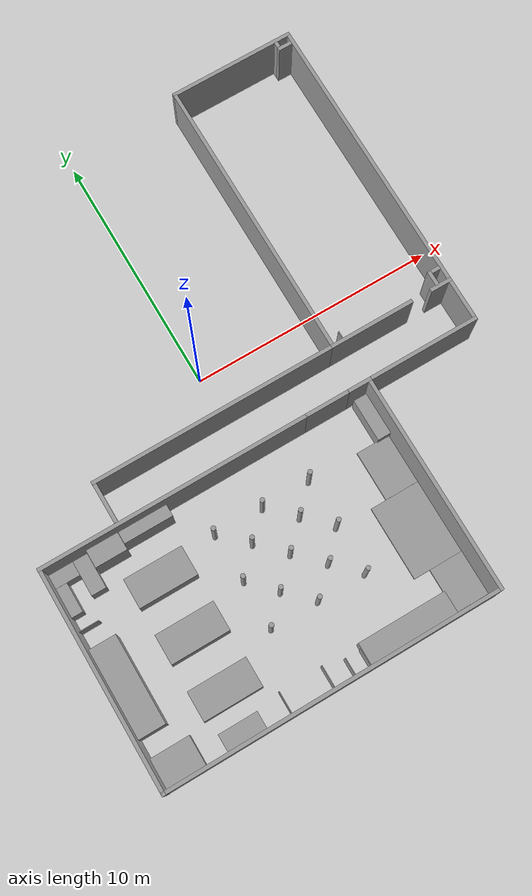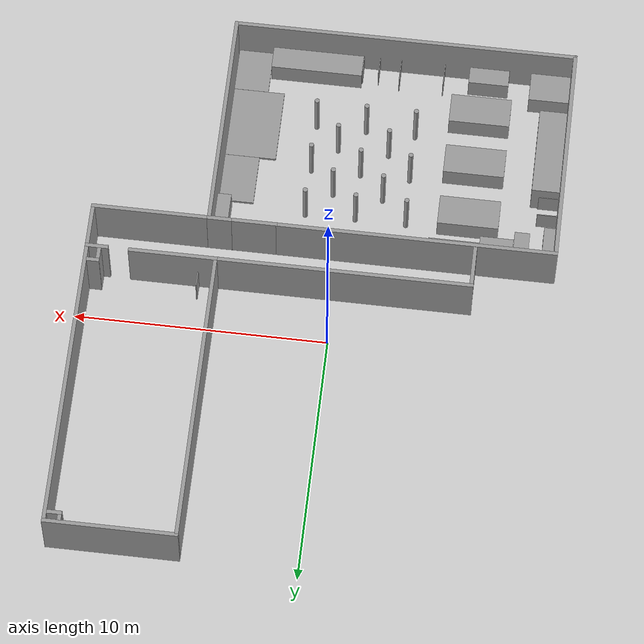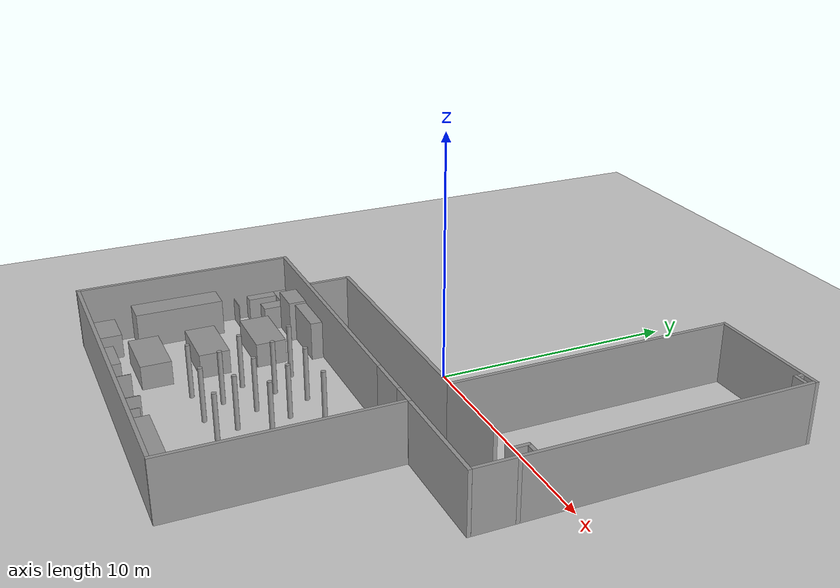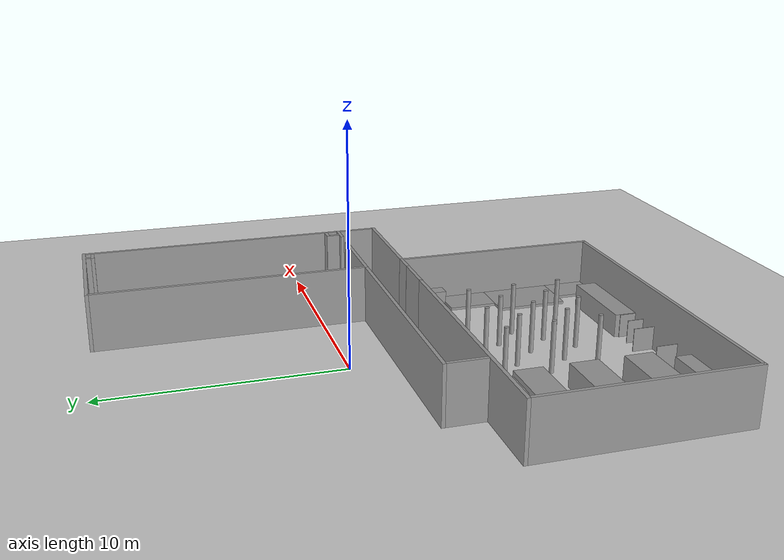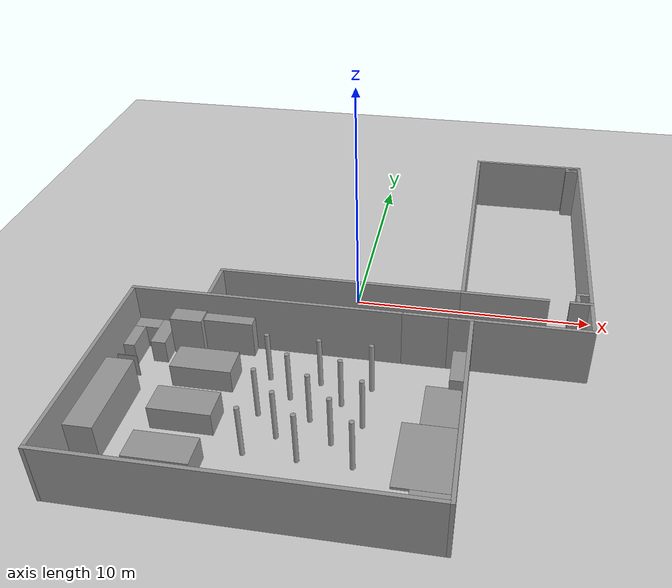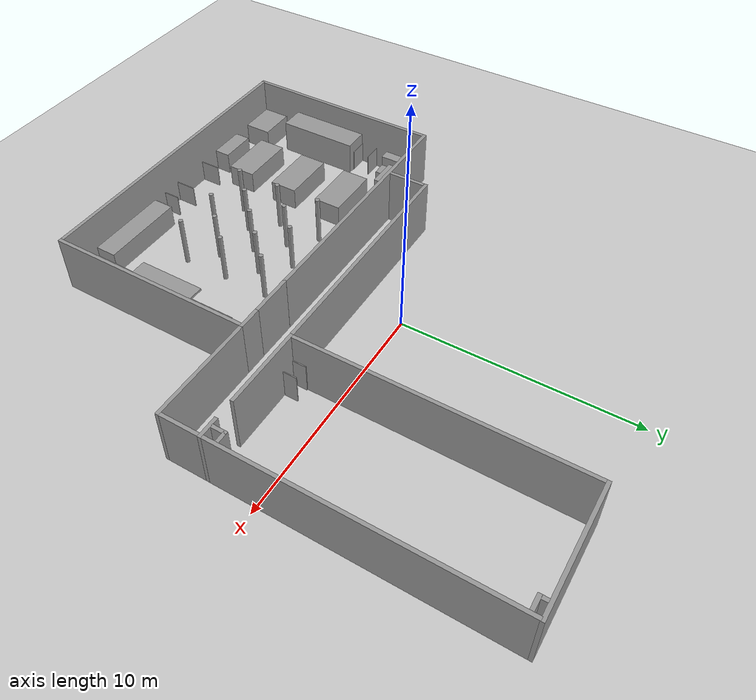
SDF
<sdf version="1.6">
 <world name="default">
  <light name="sun" type="directional">
   <pose>0 0 10 0 -0 0</pose>
   <diffuse>0.8 0.8 0.8 1</diffuse>
   <specular>0.2 0.2 0.2 1</specular>
   <attenuation>
    <range>1000</range>
    <constant>0.9</constant>
    <linear>0.01</linear>
    <quadratic>0.001</quadratic>
   </attenuation>
   <direction>-0.5 0.1 -0.9</direction>
  </light>
  <model name="ground_plane">
   <static>1</static>
   <link name="link">
    <collision name="collision">
     <geometry><plane><normal>0 0 1</normal><size>100 100</size></plane></geometry>
     <surface>
      <contact><collide_bitmask>65535</collide_bitmask></contact>
      <friction><ode><mu>1</mu><mu2>1</mu2></ode></friction>
     </surface>
    </collision>
    <visual name="visual">
     <cast_shadows>0</cast_shadows>
     <geometry><plane><normal>0 0 1</normal><size>100 100</size></plane></geometry>
     <material>
      <script><uri>file://media/materials/scripts/gazebo.material</uri><name>Gazebo/Grey</name></script>
     </material>
    </visual>
   </link>
  </model>
  <gravity>0 0 -9.8</gravity>
  <magnetic_field>6e-06 2.3e-05 -4.2e-05</magnetic_field>
  <atmosphere type="adiabatic"/>
  <physics name="default_physics" default="0" type="ode">
   <max_step_size>0.001</max_step_size>
   <real_time_factor>1</real_time_factor>
   <real_time_update_rate>1000</real_time_update_rate>
  </physics>
  <scene><ambient>0.4 0.4 0.4 1</ambient><background>0.7 0.7 0.7 1</background><shadows>1</shadows></scene>
  <audio><device>default</device></audio>
  <spherical_coordinates>
   <surface_model>EARTH_WGS84</surface_model>
   <latitude_deg>0</latitude_deg>
   <longitude_deg>0</longitude_deg>
   <elevation>0</elevation>
   <heading_deg>0</heading_deg>
  </spherical_coordinates>
  <model name="frame_503">
   <pose>7.129 3.88164 0 0 -0 0</pose>
   <link name="Wall_10">
    <collision name="Wall_10_Collision">
     <geometry><box><size>11.57 0.15 2.5</size></box></geometry>
     <pose>0 0 1.25 0 -0 0</pose>
    </collision>
    <visual name="Wall_10_Visual">
     <pose>0 0 1.25 0 -0 0</pose>
     <geometry><box><size>11.57 0.15 2.5</size></box></geometry>
     <material>
      <script><uri>file://media/materials/scripts/gazebo.material</uri><name>Gazebo/Grey</name></script>
      <ambient>1 1 1 1</ambient>
     </material>
     <meta><layer>0</layer></meta>
    </visual>
    <pose>2.5249 0.014025 0 0 -0 -1.5708</pose>
   </link>
   <link name="Wall_16">
    <collision name="Wall_16_Collision">
     <geometry><box><size>0.915 0.15 2.5</size></box></geometry>
     <pose>0 0 1.25 0 -0 0</pose>
    </collision>
    <visual name="Wall_16_Visual">
     <pose>0 0 1.25 0 -0 0</pose>
     <geometry><box><size>0.915 0.15 2.5</size></box></geometry>
     <material>
      <script><uri>file://media/materials/scripts/gazebo.material</uri><name>Gazebo/Grey</name></script>
      <ambient>1 1 1 1</ambient>
     </material>
     <meta><layer>0</layer></meta>
    </visual>
    <pose>2.1424 -5.84133 0 0 -0 0</pose>
   </link>
   <link name="Wall_18">
    <collision name="Wall_18_Collision">
     <geometry><box><size>0.61 0.15 2.5</size></box></geometry>
     <pose>0 0 1.25 0 -0 0</pose>
    </collision>
    <visual name="Wall_18_Visual">
     <pose>0 0 1.25 0 -0 0</pose>
     <geometry><box><size>0.61 0.15 2.5</size></box></geometry>
     <material>
      <script><uri>file://media/materials/scripts/gazebo.material</uri><name>Gazebo/Grey</name></script>
      <ambient>1 1 1 1</ambient>
     </material>
     <meta><layer>0</layer></meta>
    </visual>
    <pose>2.02787 -5.48355 0 0 -0 -1.5708</pose>
   </link>
   <link name="Wall_20">
    <collision name="Wall_20_Collision">
     <geometry><box><size>0.515 0.15 2.5</size></box></geometry>
     <pose>0 0 1.25 0 -0 0</pose>
    </collision>
    <visual name="Wall_20_Visual">
     <pose>0 0 1.25 0 -0 0</pose>
     <geometry><box><size>0.515 0.15 2.5</size></box></geometry>
     <material>
      <script><uri>file://media/materials/scripts/gazebo.material</uri><name>Gazebo/Grey</name></script>
      <ambient>1 1 1 1</ambient>
     </material>
     <meta><layer>0</layer></meta>
    </visual>
    <pose>2.21248 -5.24119 0 0 -0 0</pose>
   </link>
   <link name="Wall_22">
    <collision name="Wall_22_Collision">
     <geometry><box><size>3.5 0.15 2.5</size></box></geometry>
     <pose>0 0 1.25 0 -0 0</pose>
    </collision>
    <visual name="Wall_22_Visual">
     <pose>0 0 1.25 0 -0 0</pose>
     <geometry><box><size>3.5 0.15 2.5</size></box></geometry>
     <material>
      <script><uri>file://media/materials/scripts/gazebo.material</uri><name>Gazebo/Grey</name></script>
      <ambient>1 1 1 1</ambient>
     </material>
     <meta><layer>0</layer></meta>
    </visual>
    <pose>-0.849025 -5.83136 0 0 -0 0</pose>
   </link>
   <link name="Wall_27">
    <collision name="Wall_27_Collision">
     <geometry><box><size>0.23 0.15 2.5</size></box></geometry>
     <pose>0 0 1.25 0 -0 0</pose>
    </collision>
    <visual name="Wall_27_Visual">
     <pose>0 0 1.25 0 -0 0</pose>
     <geometry><box><size>0.23 0.15 2.5</size></box></geometry>
     <material>
      <script><uri>file://media/materials/scripts/gazebo.material</uri><name>Gazebo/Grey</name></script>
      <ambient>1 1 1 1</ambient>
     </material>
     <meta><layer>0</layer></meta>
    </visual>
    <pose>1.94245 5.66179 0 0 -0 -1.5708</pose>
   </link>
   <link name="Wall_29">
    <collision name="Wall_29_Collision">
     <geometry><box><size>0.59 0.15 2.5</size></box></geometry>
     <pose>0 0 1.25 0 -0 0</pose>
    </collision>
    <visual name="Wall_29_Visual">
     <pose>0 0 1.25 0 -0 0</pose>
     <geometry><box><size>0.59 0.15 2.5</size></box></geometry>
     <material>
      <script><uri>file://media/materials/scripts/gazebo.material</uri><name>Gazebo/Grey</name></script>
      <ambient>1 1 1 1</ambient>
     </material>
     <meta><layer>0</layer></meta>
    </visual>
    <pose>2.16053 5.47077 0 0 -0 0</pose>
   </link>
   <link name="Wall_33">
    <collision name="Wall_33_Collision">
     <geometry><box><size>0.57 0.04 1.3</size></box></geometry>
     <pose>0 0 0.65 0 -0 0</pose>
    </collision>
    <visual name="Wall_33_Visual">
     <pose>0 0 0.65 0 -0 0</pose>
     <geometry><box><size>0.57 0.04 1.3</size></box></geometry>
     <material>
      <script><uri>file://media/materials/scripts/gazebo.material</uri><name>Gazebo/Grey</name></script>
      <ambient>1 1 1 1</ambient>
     </material>
     <meta><layer>0</layer></meta>
    </visual>
    <pose>-2.42208 -5.46511 0 0 -0 -1.5708</pose>
   </link>
   <link name="Wall_35">
    <collision name="Wall_35_Collision">
     <geometry><box><size>0.57 0.04 1.3</size></box></geometry>
     <pose>0 0 0.65 0 -0 0</pose>
    </collision>
    <visual name="Wall_35_Visual">
     <pose>0 0 0.65 0 -0 0</pose>
     <geometry><box><size>0.57 0.04 1.3</size></box></geometry>
     <material>
      <script><uri>file://media/materials/scripts/gazebo.material</uri><name>Gazebo/Grey</name></script>
      <ambient>1 1 1 1</ambient>
     </material>
     <meta><layer>0</layer></meta>
    </visual>
    <pose>-1.81841 -5.4653 0 0 -0 -1.5708</pose>
   </link>
   <link name="Wall_6">
    <collision name="Wall_6_Collision">
     <geometry><box><size>5.2 0.15 2.5</size></box></geometry>
     <pose>0 0 1.25 0 -0 0</pose>
    </collision>
    <visual name="Wall_6_Visual">
     <pose>0 0 1.25 0 -0 0</pose>
     <geometry><box><size>5.2 0.15 2.5</size></box></geometry>
     <material>
      <script><uri>file://media/materials/scripts/gazebo.material</uri><name>Gazebo/Grey</name></script>
      <ambient>1 1 1 1</ambient>
     </material>
     <meta><layer>0</layer></meta>
    </visual>
    <pose>0 5.84133 0 0 -0 0</pose>
   </link>
   <link name="Wall_8">
    <collision name="Wall_8_Collision">
     <geometry><box><size>11.57 0.15 2.5</size></box></geometry>
     <pose>0 0 1.25 0 -0 0</pose>
    </collision>
    <visual name="Wall_8_Visual">
     <pose>0 0 1.25 0 -0 0</pose>
     <geometry><box><size>11.57 0.15 2.5</size></box></geometry>
     <material>
      <script><uri>file://media/materials/scripts/gazebo.material</uri><name>Gazebo/Grey</name></script>
      <ambient>1 1 1 1</ambient>
     </material>
     <meta><layer>0</layer></meta>
    </visual>
    <pose>-2.52426 0.021404 0 0 -0 -1.5708</pose>
   </link>
   <static>1</static>
  </model>
  <model name="aisle1">
   <pose>9.65276 -2.82844 0 0 -0 0</pose>
   <link name="Wall_2">
    <collision name="Wall_2_Collision">
     <geometry><box><size>1.6 0.15 2.5</size></box></geometry>
     <pose>0 0 1.25 0 -0 0</pose>
    </collision>
    <visual name="Wall_2_Visual">
     <pose>0 0 1.25 0 -0 0</pose>
     <geometry><box><size>1.6 0.15 2.5</size></box></geometry>
     <material>
      <script><uri>file://media/materials/scripts/gazebo.material</uri><name>Gazebo/Grey</name></script>
      <ambient>1 1 1 1</ambient>
     </material>
     <meta><layer>0</layer></meta>
    </visual>
    <pose>0 -0 0 0 -0 -1.5708</pose>
   </link>
   <static>1</static>
  </model>
  <model name="a2">
   <pose>7.44595 -3.70134 0 0 -0 0</pose>
   <link name="Wall_7">
    <collision name="Wall_7_Collision">
     <geometry><box><size>4.56 0.15 2.5</size></box></geometry>
     <pose>0 0 1.25 0 -0 0</pose>
    </collision>
    <visual name="Wall_7_Visual">
     <pose>0 0 1.25 0 -0 0</pose>
     <geometry><box><size>4.56 0.15 2.5</size></box></geometry>
     <material>
      <script><uri>file://media/materials/scripts/gazebo.material</uri><name>Gazebo/Grey</name></script>
      <ambient>1 1 1 1</ambient>
     </material>
     <meta><layer>0</layer></meta>
    </visual>
   </link>
   <static>1</static>
  </model>
  <model name="a3">
   <pose>5.08575 -8.18004 0 0 -0 0</pose>
   <link name="Wall_10">
    <collision name="Wall_10_Collision">
     <geometry><box><size>8.82 0.15 2.5</size></box></geometry>
     <pose>0 0 1.25 0 -0 0</pose>
    </collision>
    <visual name="Wall_10_Visual">
     <pose>0 0 1.25 0 -0 0</pose>
     <geometry><box><size>8.82 0.15 2.5</size></box></geometry>
     <material>
      <script><uri>file://media/materials/scripts/gazebo.material</uri><name>Gazebo/Grey</name></script>
      <ambient>1 1 1 1</ambient>
     </material>
     <meta><layer>0</layer></meta>
    </visual>
    <pose>0 -0 0 0 -0 -1.5708</pose>
   </link>
   <static>1</static>
  </model>
  <model name="a4">
   <pose>-1.78326 -12.5146 0 0 -0 0</pose>
   <link name="Wall_12">
    <collision name="Wall_12_Collision">
     <geometry><box><size>13.62 0.15 2.5</size></box></geometry>
     <pose>0 0 1.25 0 -0 0</pose>
    </collision>
    <visual name="Wall_12_Visual">
     <pose>0 0 1.25 0 -0 0</pose>
     <geometry><box><size>13.62 0.15 2.5</size></box></geometry>
     <material>
      <script><uri>file://media/materials/scripts/gazebo.material</uri><name>Gazebo/Grey</name></script>
      <ambient>1 1 1 1</ambient>
     </material>
     <meta><layer>0</layer></meta>
    </visual>
   </link>
   <static>1</static>
  </model>
  <model name="a3_clone">
   <pose>-8.5273 -8.18669 0 0 -0 0</pose>
   <link name="Wall_10">
    <collision name="Wall_10_Collision">
     <geometry><box><size>8.82 0.15 2.5</size></box></geometry>
     <pose>0 0 1.25 0 -0 0</pose>
    </collision>
    <visual name="Wall_10_Visual">
     <pose>0 0 1.25 0 -0 0</pose>
     <geometry><box><size>8.82 0.15 2.5</size></box></geometry>
     <material>
      <script><uri>file://media/materials/scripts/gazebo.material</uri><name>Gazebo/Grey</name></script>
      <ambient>1 1 1 1</ambient>
     </material>
     <meta><layer>0</layer></meta>
    </visual>
    <pose>0 -0 0 0 -0 -1.5708</pose>
   </link>
   <static>1</static>
  </model>
  <model name="a5">
   <pose>4.68026 -3.70193 0 0 -0 0</pose>
   <link name="Wall_16">
    <collision name="Wall_16_Collision">
     <geometry><box><size>0.97 0.15 2.5</size></box></geometry>
     <pose>0 0 1.25 0 -0 0</pose>
    </collision>
    <visual name="Wall_16_Visual">
     <pose>0 0 1.25 0 -0 0</pose>
     <geometry><box><size>0.97 0.15 2.5</size></box></geometry>
     <material>
      <script><uri>file://media/materials/scripts/gazebo.material</uri><name>Gazebo/Grey</name></script>
      <ambient>1 1 1 1</ambient>
     </material>
     <meta><layer>0</layer></meta>
    </visual>
   </link>
   <static>1</static>
  </model>
  <model name="aisle6">
   <pose>-3.07982 -3.70444 0 0 -0 0</pose>
   <link name="Wall_22">
    <collision name="Wall_22_Collision">
     <geometry><box><size>11.05 0.15 2.5</size></box></geometry>
     <pose>0 0 1.25 0 -0 0</pose>
    </collision>
    <visual name="Wall_22_Visual">
     <pose>0 0 1.25 0 -0 0</pose>
     <geometry><box><size>11.05 0.15 2.5</size></box></geometry>
     <material>
      <script><uri>file://media/materials/scripts/gazebo.material</uri><name>Gazebo/Grey</name></script>
      <ambient>1 1 1 1</ambient>
     </material>
     <meta><layer>0</layer></meta>
    </visual>
   </link>
   <static>1</static>
  </model>
  <model name="aisle1_clone">
   <pose>-5.38806 -2.82651 0 0 -0 0</pose>
   <link name="Wall_2">
    <collision name="Wall_2_Collision">
     <geometry><box><size>1.6 0.15 2.5</size></box></geometry>
     <pose>0 0 1.25 0 -0 0</pose>
    </collision>
    <visual name="Wall_2_Visual">
     <pose>0 0 1.25 0 -0 0</pose>
     <geometry><box><size>1.6 0.15 2.5</size></box></geometry>
     <material>
      <script><uri>file://media/materials/scripts/gazebo.material</uri><name>Gazebo/Grey</name></script>
      <ambient>1 1 1 1</ambient>
     </material>
     <meta><layer>0</layer></meta>
    </visual>
    <pose>0 -0 0 0 -0 -1.5708</pose>
   </link>
   <static>1</static>
  </model>
  <model name="a7_0">
   <pose>-0.468482 -1.9505 0 0 -0 0</pose>
   <link name="Wall_44">
    <collision name="Wall_44_Collision">
     <geometry><box><size>10 0.15 2.5</size></box></geometry>
     <pose>0 0 1.25 0 -0 0</pose>
    </collision>
    <visual name="Wall_44_Visual">
     <pose>0 0 1.25 0 -0 0</pose>
     <geometry><box><size>10 0.15 2.5</size></box></geometry>
     <material>
      <script><uri>file://media/materials/scripts/gazebo.material</uri><name>Gazebo/Grey</name></script>
      <ambient>1 1 1 1</ambient>
     </material>
     <meta><layer>0</layer></meta>
    </visual>
   </link>
   <static>1</static>
  </model>
  <model name="unit_box_5">
   <link name="link">
    <inertial>
     <mass>10</mass>
     <inertia>
      <ixx>0.166667</ixx>
      <ixy>0</ixy>
      <ixz>0</ixz>
      <iyy>0.166667</iyy>
      <iyz>0</iyz>
      <izz>0.166667</izz>
     </inertia>
    </inertial>
    <visual name="visual">
     <geometry><box><size>1.6 1.2 1</size></box></geometry>
     <material>
      <script><name>Gazebo/Grey</name><uri>file://media/materials/scripts/gazebo.material</uri></script>
      <shader type="vertex"><normal_map>__default__</normal_map></shader>
      <ambient>0.3 0.3 0.3 1</ambient>
      <diffuse>0.7 0.7 0.7 1</diffuse>
      <specular>0.01 0.01 0.01 1</specular>
      <emissive>0 0 0 1</emissive>
     </material>
    </visual>
    <collision name="collision">
     <geometry><box><size>1 1 1</size></box></geometry>
     <surface>
      <friction>
       <ode><mu>1</mu><mu2>1</mu2><fdir1>0 0 0</fdir1><slip1>0</slip1><slip2>0</slip2></ode>
       <torsional>
        <coefficient>1</coefficient>
        <patch_radius>0</patch_radius>
        <surface_radius>0</surface_radius>
        <use_patch_radius>1</use_patch_radius>
        <ode><slip>0</slip></ode>
       </torsional>
      </friction>
      <bounce><restitution_coefficient>0</restitution_coefficient><threshold>1e+06</threshold></bounce>
      <contact>
       <collide_without_contact>0</collide_without_contact>
       <collide_without_contact_bitmask>1</collide_without_contact_bitmask>
       <collide_bitmask>1</collide_bitmask>
       <ode>
        <soft_cfm>0</soft_cfm>
        <soft_erp>0.2</soft_erp>
        <kp>1e+13</kp>
        <kd>1</kd>
        <max_vel>0.01</max_vel>
        <min_depth>0</min_depth>
       </ode>
       <bullet>
        <split_impulse>1</split_impulse>
        <split_impulse_penetration_threshold>-0.01</split_impulse_penetration_threshold>
        <soft_cfm>0</soft_cfm>
        <soft_erp>0.2</soft_erp>
        <kp>1e+13</kp>
        <kd>1</kd>
       </bullet>
      </contact>
     </surface>
    </collision>
   </link>
   <static>0</static>
   <pose>-7.6506 -11.826 0.5 0 -2e-06 0</pose>
  </model>
  <model name="step1">
   <static>1</static>
   <link name="link">
    <inertial>
     <mass>10</mass>
     <inertia>
      <ixx>0.166667</ixx>
      <ixy>0</ixy>
      <ixz>0</ixz>
      <iyy>0.166667</iyy>
      <iyz>0</iyz>
      <izz>0.166667</izz>
     </inertia>
    </inertial>
    <visual name="visual">
     <geometry><box><size>1.38 1.80435 0.11</size></box></geometry>
     <material>
      <script><name>Gazebo/Grey</name><uri>file://media/materials/scripts/gazebo.material</uri></script>
      <shader type="vertex"><normal_map>__default__</normal_map></shader>
      <ambient>0.3 0.3 0.3 1</ambient>
      <diffuse>0.7 0.7 0.7 1</diffuse>
      <specular>0.01 0.01 0.01 1</specular>
      <emissive>0 0 0 1</emissive>
     </material>
    </visual>
    <collision name="collision">
     <geometry><box><size>1 0.880167 1</size></box></geometry>
     <surface>
      <friction>
       <ode><mu>1</mu><mu2>1</mu2><fdir1>0 0 0</fdir1><slip1>0</slip1><slip2>0</slip2></ode>
       <torsional>
        <coefficient>1</coefficient>
        <patch_radius>0</patch_radius>
        <surface_radius>0</surface_radius>
        <use_patch_radius>1</use_patch_radius>
        <ode><slip>0</slip></ode>
       </torsional>
      </friction>
      <bounce><restitution_coefficient>0</restitution_coefficient><threshold>1e+06</threshold></bounce>
      <contact>
       <collide_without_contact>0</collide_without_contact>
       <collide_without_contact_bitmask>1</collide_without_contact_bitmask>
       <collide_bitmask>1</collide_bitmask>
       <ode>
        <soft_cfm>0</soft_cfm>
        <soft_erp>0.2</soft_erp>
        <kp>1e+13</kp>
        <kd>1</kd>
        <max_vel>0.01</max_vel>
        <min_depth>0</min_depth>
       </ode>
       <bullet>
        <split_impulse>1</split_impulse>
        <split_impulse_penetration_threshold>-0.01</split_impulse_penetration_threshold>
        <soft_cfm>0</soft_cfm>
        <soft_erp>0.2</soft_erp>
        <kp>1e+13</kp>
        <kd>1</kd>
       </bullet>
      </contact>
     </surface>
    </collision>
   </link>
   <pose>4.28124 -11.4927 0.499995 1e-05 -0 0</pose>
  </model>
  <model name="step3">
   <static>1</static>
   <link name="link">
    <inertial>
     <mass>10</mass>
     <inertia>
      <ixx>0.166667</ixx>
      <ixy>0</ixy>
      <ixz>0</ixz>
      <iyy>0.166667</iyy>
      <iyz>0</iyz>
      <izz>0.166667</izz>
     </inertia>
    </inertial>
    <visual name="visual">
     <geometry><box><size>2.03 3.01 0.11</size></box></geometry>
     <material>
      <script><name>Gazebo/Grey</name><uri>file://media/materials/scripts/gazebo.material</uri></script>
      <shader type="vertex"><normal_map>__default__</normal_map></shader>
      <ambient>0.3 0.3 0.3 1</ambient>
      <diffuse>0.7 0.7 0.7 1</diffuse>
      <specular>0.01 0.01 0.01 1</specular>
      <emissive>0 0 0 1</emissive>
     </material>
    </visual>
    <collision name="collision">
     <geometry><box><size>1 1 1</size></box></geometry>
     <surface>
      <friction>
       <ode><mu>1</mu><mu2>1</mu2><fdir1>0 0 0</fdir1><slip1>0</slip1><slip2>0</slip2></ode>
       <torsional>
        <coefficient>1</coefficient>
        <patch_radius>0</patch_radius>
        <surface_radius>0</surface_radius>
        <use_patch_radius>1</use_patch_radius>
        <ode><slip>0</slip></ode>
       </torsional>
      </friction>
      <bounce><restitution_coefficient>0</restitution_coefficient><threshold>1e+06</threshold></bounce>
      <contact>
       <collide_without_contact>0</collide_without_contact>
       <collide_without_contact_bitmask>1</collide_without_contact_bitmask>
       <collide_bitmask>1</collide_bitmask>
       <ode>
        <soft_cfm>0</soft_cfm>
        <soft_erp>0.2</soft_erp>
        <kp>1e+13</kp>
        <kd>1</kd>
        <max_vel>0.01</max_vel>
        <min_depth>0</min_depth>
       </ode>
       <bullet>
        <split_impulse>1</split_impulse>
        <split_impulse_penetration_threshold>-0.01</split_impulse_penetration_threshold>
        <soft_cfm>0</soft_cfm>
        <soft_erp>0.2</soft_erp>
        <kp>1e+13</kp>
        <kd>1</kd>
       </bullet>
      </contact>
     </surface>
    </collision>
   </link>
   <pose>3.95023 -9.08446 0.499995 1e-05 -0 0</pose>
  </model>
  <model name="funi3">
   <static>1</static>
   <link name="link">
    <inertial>
     <mass>10</mass>
     <inertia>
      <ixx>0.166667</ixx>
      <ixy>0</ixy>
      <ixz>0</ixz>
      <iyy>0.166667</iyy>
      <iyz>0</iyz>
      <izz>0.166667</izz>
     </inertia>
    </inertial>
    <pose>-1.31903 0.055597 0 0 -0 0</pose>
    <visual name="visual">
     <geometry><box><size>3.65 0.910525 1</size></box></geometry>
     <material>
      <script><name>Gazebo/Grey</name><uri>file://media/materials/scripts/gazebo.material</uri></script>
      <shader type="vertex"><normal_map>__default__</normal_map></shader>
      <ambient>0.3 0.3 0.3 1</ambient>
      <diffuse>0.7 0.7 0.7 1</diffuse>
      <specular>0.01 0.01 0.01 1</specular>
      <emissive>0 0 0 1</emissive>
     </material>
    </visual>
    <collision name="collision">
     <geometry><box><size>1 0.790525 1</size></box></geometry>
     <surface>
      <friction>
       <ode><mu>1</mu><mu2>1</mu2><fdir1>0 0 0</fdir1><slip1>0</slip1><slip2>0</slip2></ode>
       <torsional>
        <coefficient>1</coefficient>
        <patch_radius>0</patch_radius>
        <surface_radius>0</surface_radius>
        <use_patch_radius>1</use_patch_radius>
        <ode><slip>0</slip></ode>
       </torsional>
      </friction>
      <bounce><restitution_coefficient>0</restitution_coefficient><threshold>1e+06</threshold></bounce>
      <contact>
       <collide_without_contact>0</collide_without_contact>
       <collide_without_contact_bitmask>1</collide_without_contact_bitmask>
       <collide_bitmask>1</collide_bitmask>
       <ode>
        <soft_cfm>0</soft_cfm>
        <soft_erp>0.2</soft_erp>
        <kp>1e+13</kp>
        <kd>1</kd>
        <max_vel>0.01</max_vel>
        <min_depth>0</min_depth>
       </ode>
       <bullet>
        <split_impulse>1</split_impulse>
        <split_impulse_penetration_threshold>-0.01</split_impulse_penetration_threshold>
        <soft_cfm>0</soft_cfm>
        <soft_erp>0.2</soft_erp>
        <kp>1e+13</kp>
        <kd>1</kd>
       </bullet>
      </contact>
     </surface>
    </collision>
   </link>
   <pose>3.07038 -12.0343 0.499982 -0 1e-05 -8.9e-05</pose>
  </model>
  <model name="step2">
   <static>1</static>
   <link name="link">
    <inertial>
     <mass>10</mass>
     <inertia>
      <ixx>0.166667</ixx>
      <ixy>0</ixy>
      <ixz>0</ixz>
      <iyy>0.166667</iyy>
      <iyz>0</iyz>
      <izz>0.166667</izz>
     </inertia>
    </inertial>
    <visual name="visual">
     <geometry><box><size>1.38 2.05001 0.11</size></box></geometry>
     <material>
      <script><name>Gazebo/Grey</name><uri>file://media/materials/scripts/gazebo.material</uri></script>
      <shader type="vertex"><normal_map>__default__</normal_map></shader>
      <ambient>0.3 0.3 0.3 1</ambient>
      <diffuse>0.7 0.7 0.7 1</diffuse>
      <specular>0.01 0.01 0.01 1</specular>
      <emissive>0 0 0 1</emissive>
     </material>
    </visual>
    <collision name="collision">
     <geometry><box><size>1 0.999999 1</size></box></geometry>
     <surface>
      <friction>
       <ode><mu>1</mu><mu2>1</mu2><fdir1>0 0 0</fdir1><slip1>0</slip1><slip2>0</slip2></ode>
       <torsional>
        <coefficient>1</coefficient>
        <patch_radius>0</patch_radius>
        <surface_radius>0</surface_radius>
        <use_patch_radius>1</use_patch_radius>
        <ode><slip>0</slip></ode>
       </torsional>
      </friction>
      <bounce><restitution_coefficient>0</restitution_coefficient><threshold>1e+06</threshold></bounce>
      <contact>
       <collide_without_contact>0</collide_without_contact>
       <collide_without_contact_bitmask>1</collide_without_contact_bitmask>
       <collide_bitmask>1</collide_bitmask>
       <ode>
        <soft_cfm>0</soft_cfm>
        <soft_erp>0.2</soft_erp>
        <kp>1e+13</kp>
        <kd>1</kd>
        <max_vel>0.01</max_vel>
        <min_depth>0</min_depth>
       </ode>
       <bullet>
        <split_impulse>1</split_impulse>
        <split_impulse_penetration_threshold>-0.01</split_impulse_penetration_threshold>
        <soft_cfm>0</soft_cfm>
        <soft_erp>0.2</soft_erp>
        <kp>1e+13</kp>
        <kd>1</kd>
       </bullet>
      </contact>
     </surface>
    </collision>
   </link>
   <pose>4.27379 -6.55381 0.499995 -1e-05 0 0</pose>
  </model>
  <model name="deskframe">
   <static>1</static>
   <link name="Wall_34">
    <pose>-0.325 0 0 0 0 -1.5708</pose>
    <inertial>
     <mass>10</mass>
     <inertia><ixx>1</ixx><ixy>0</ixy><ixz>0</ixz><iyy>1</iyy><iyz>0</iyz><izz>1</izz></inertia>
    </inertial>
    <visual name="Wall_34_Visual">
     <pose>0 0 1.25 0 -0 0</pose>
     <geometry><box><size>0.7 0.03 1</size></box></geometry>
     <material>
      <script><uri>file://media/materials/scripts/gazebo.material</uri><name>Gazebo/Grey</name></script>
      <ambient>1 1 1 1</ambient>
      <shader type="vertex"><normal_map>__default__</normal_map></shader>
      <diffuse>0.7 0.7 0.7 1</diffuse>
      <specular>0.01 0.01 0.01 1</specular>
      <emissive>0 0 0 1</emissive>
     </material>
     <meta><layer>0</layer></meta>
    </visual>
    <collision name="Wall_34_Collision">
     <pose>0 0 1.25 0 -0 0</pose>
     <geometry><box><size>0.7 0.15 2.5</size></box></geometry>
     <surface>
      <friction>
       <ode><mu>1</mu><mu2>1</mu2><fdir1>0 0 0</fdir1><slip1>0</slip1><slip2>0</slip2></ode>
       <torsional>
        <coefficient>1</coefficient>
        <patch_radius>0</patch_radius>
        <surface_radius>0</surface_radius>
        <use_patch_radius>1</use_patch_radius>
        <ode><slip>0</slip></ode>
       </torsional>
      </friction>
      <bounce><restitution_coefficient>0</restitution_coefficient><threshold>1e+06</threshold></bounce>
      <contact>
       <collide_without_contact>0</collide_without_contact>
       <collide_without_contact_bitmask>1</collide_without_contact_bitmask>
       <collide_bitmask>1</collide_bitmask>
       <ode>
        <soft_cfm>0</soft_cfm>
        <soft_erp>0.2</soft_erp>
        <kp>1e+13</kp>
        <kd>1</kd>
        <max_vel>0.01</max_vel>
        <min_depth>0</min_depth>
       </ode>
       <bullet>
        <split_impulse>1</split_impulse>
        <split_impulse_penetration_threshold>-0.01</split_impulse_penetration_threshold>
        <soft_cfm>0</soft_cfm>
        <soft_erp>0.2</soft_erp>
        <kp>1e+13</kp>
        <kd>1</kd>
       </bullet>
      </contact>
     </surface>
    </collision>
   </link>
   <link name="Wall_38">
    <pose>0.325 0 0 0 0 -1.5708</pose>
    <inertial>
     <mass>0.400397</mass>
     <inertia>
      <ixx>0.20866</ixx>
      <ixy>0</ixy>
      <ixz>0</ixz>
      <iyy>0.22489</iyy>
      <iyz>0</iyz>
      <izz>0.0164699</izz>
     </inertia>
    </inertial>
    <visual name="Wall_38_Visual">
     <pose>0 0 1.25 0 -0 0</pose>
     <geometry><box><size>0.7 0.030001 1</size></box></geometry>
     <material>
      <script><uri>file://media/materials/scripts/gazebo.material</uri><name>Gazebo/Grey</name></script>
      <ambient>1 1 1 1</ambient>
      <shader type="vertex"><normal_map>__default__</normal_map></shader>
      <diffuse>0.7 0.7 0.7 1</diffuse>
      <specular>0.01 0.01 0.01 1</specular>
      <emissive>0 0 0 1</emissive>
     </material>
     <meta><layer>0</layer></meta>
    </visual>
    <collision name="Wall_38_Collision">
     <pose>0 0 1.25 0 -0 0</pose>
     <geometry><box><size>0.7 0.060061 2.5</size></box></geometry>
     <surface>
      <friction>
       <ode><mu>1</mu><mu2>1</mu2><fdir1>0 0 0</fdir1><slip1>0</slip1><slip2>0</slip2></ode>
       <torsional>
        <coefficient>1</coefficient>
        <patch_radius>0</patch_radius>
        <surface_radius>0</surface_radius>
        <use_patch_radius>1</use_patch_radius>
        <ode><slip>0</slip></ode>
       </torsional>
      </friction>
      <bounce><restitution_coefficient>0</restitution_coefficient><threshold>1e+06</threshold></bounce>
      <contact>
       <collide_without_contact>0</collide_without_contact>
       <collide_without_contact_bitmask>1</collide_without_contact_bitmask>
       <collide_bitmask>1</collide_bitmask>
       <ode>
        <soft_cfm>0</soft_cfm>
        <soft_erp>0.2</soft_erp>
        <kp>1e+13</kp>
        <kd>1</kd>
        <max_vel>0.01</max_vel>
        <min_depth>0</min_depth>
       </ode>
       <bullet>
        <split_impulse>1</split_impulse>
        <split_impulse_penetration_threshold>-0.01</split_impulse_penetration_threshold>
        <soft_cfm>0</soft_cfm>
        <soft_erp>0.2</soft_erp>
        <kp>1e+13</kp>
        <kd>1</kd>
       </bullet>
      </contact>
     </surface>
    </collision>
   </link>
   <pose>-0.415536 -12.0779 -0.765953 0 -0 0</pose>
  </model>
  <model name="backfuni">
   <static>1</static>
   <link name="link">
    <inertial>
     <mass>10</mass>
     <inertia>
      <ixx>0.166667</ixx>
      <ixy>0</ixy>
      <ixz>0</ixz>
      <iyy>0.166667</iyy>
      <iyz>0</iyz>
      <izz>0.166667</izz>
     </inertia>
    </inertial>
    <visual name="visual">
     <geometry><box><size>3.6 1.1 1.5</size></box></geometry>
     <material>
      <script><name>Gazebo/Grey</name><uri>file://media/materials/scripts/gazebo.material</uri></script>
      <shader type="vertex"><normal_map>__default__</normal_map></shader>
      <ambient>0.3 0.3 0.3 1</ambient>
      <diffuse>0.7 0.7 0.7 1</diffuse>
      <specular>0.01 0.01 0.01 1</specular>
      <emissive>0 0 0 1</emissive>
     </material>
    </visual>
    <collision name="collision">
     <geometry><box><size>1 1 1</size></box></geometry>
     <surface>
      <friction>
       <ode><mu>1</mu><mu2>1</mu2><fdir1>0 0 0</fdir1><slip1>0</slip1><slip2>0</slip2></ode>
       <torsional>
        <coefficient>1</coefficient>
        <patch_radius>0</patch_radius>
        <surface_radius>0</surface_radius>
        <use_patch_radius>1</use_patch_radius>
        <ode><slip>0</slip></ode>
       </torsional>
      </friction>
      <bounce><restitution_coefficient>0</restitution_coefficient><threshold>1e+06</threshold></bounce>
      <contact>
       <collide_without_contact>0</collide_without_contact>
       <collide_without_contact_bitmask>1</collide_without_contact_bitmask>
       <collide_bitmask>1</collide_bitmask>
       <ode>
        <soft_cfm>0</soft_cfm>
        <soft_erp>0.2</soft_erp>
        <kp>1e+13</kp>
        <kd>1</kd>
        <max_vel>0.01</max_vel>
        <min_depth>0</min_depth>
       </ode>
       <bullet>
        <split_impulse>1</split_impulse>
        <split_impulse_penetration_threshold>-0.01</split_impulse_penetration_threshold>
        <soft_cfm>0</soft_cfm>
        <soft_erp>0.2</soft_erp>
        <kp>1e+13</kp>
        <kd>1</kd>
       </bullet>
      </contact>
     </surface>
    </collision>
   </link>
   <pose>-7.89809 -8.70061 0.739652 6e-06 0 -1.57022</pose>
  </model>
  <model name="deskframe2">
   <static>1</static>
   <link name="Wall_12">
    <pose>-0.385485 0.00161 0 0 0 -1.5708</pose>
    <inertial>
     <mass>10</mass>
     <inertia><ixx>1</ixx><ixy>0</ixy><ixz>0</ixz><iyy>1</iyy><iyz>0</iyz><izz>1</izz></inertia>
    </inertial>
    <visual name="Wall_12_Visual">
     <pose>0 0 1.25 0 -0 0</pose>
     <geometry><box><size>0.8 0.03 1</size></box></geometry>
     <material>
      <script><uri>file://media/materials/scripts/gazebo.material</uri><name>Gazebo/Grey</name></script>
      <ambient>1 1 1 1</ambient>
      <shader type="vertex"><normal_map>__default__</normal_map></shader>
      <diffuse>0.7 0.7 0.7 1</diffuse>
      <specular>0.01 0.01 0.01 1</specular>
      <emissive>0 0 0 1</emissive>
     </material>
     <meta><layer>0</layer></meta>
    </visual>
    <collision name="Wall_12_Collision">
     <pose>0 0 1.25 0 -0 0</pose>
     <geometry><box><size>0.8 0.03 2.5</size></box></geometry>
     <surface>
      <friction>
       <ode><mu>1</mu><mu2>1</mu2><fdir1>0 0 0</fdir1><slip1>0</slip1><slip2>0</slip2></ode>
       <torsional>
        <coefficient>1</coefficient>
        <patch_radius>0</patch_radius>
        <surface_radius>0</surface_radius>
        <use_patch_radius>1</use_patch_radius>
        <ode><slip>0</slip></ode>
       </torsional>
      </friction>
      <bounce><restitution_coefficient>0</restitution_coefficient><threshold>1e+06</threshold></bounce>
      <contact>
       <collide_without_contact>0</collide_without_contact>
       <collide_without_contact_bitmask>1</collide_without_contact_bitmask>
       <collide_bitmask>1</collide_bitmask>
       <ode>
        <soft_cfm>0</soft_cfm>
        <soft_erp>0.2</soft_erp>
        <kp>1e+13</kp>
        <kd>1</kd>
        <max_vel>0.01</max_vel>
        <min_depth>0</min_depth>
       </ode>
       <bullet>
        <split_impulse>1</split_impulse>
        <split_impulse_penetration_threshold>-0.01</split_impulse_penetration_threshold>
        <soft_cfm>0</soft_cfm>
        <soft_erp>0.2</soft_erp>
        <kp>1e+13</kp>
        <kd>1</kd>
       </bullet>
      </contact>
     </surface>
    </collision>
   </link>
   <link name="Wall_23">
    <pose>0.385485 -0.00161 0 0 0 -1.5708</pose>
    <inertial>
     <mass>10</mass>
     <inertia><ixx>1</ixx><ixy>0</ixy><ixz>0</ixz><iyy>1</iyy><iyz>0</iyz><izz>1</izz></inertia>
    </inertial>
    <visual name="Wall_23_Visual">
     <pose>0 0 1.25 0 -0 0</pose>
     <geometry><box><size>0.8 0.03 1</size></box></geometry>
     <material>
      <script><uri>file://media/materials/scripts/gazebo.material</uri><name>Gazebo/Grey</name></script>
      <ambient>1 1 1 1</ambient>
      <shader type="vertex"><normal_map>__default__</normal_map></shader>
      <diffuse>0.7 0.7 0.7 1</diffuse>
      <specular>0.01 0.01 0.01 1</specular>
      <emissive>0 0 0 1</emissive>
     </material>
     <meta><layer>0</layer></meta>
    </visual>
    <collision name="Wall_23_Collision">
     <pose>0 0 1.25 0 -0 0</pose>
     <geometry><box><size>0.8 0.03 2.5</size></box></geometry>
     <surface>
      <friction>
       <ode><mu>1</mu><mu2>1</mu2><fdir1>0 0 0</fdir1><slip1>0</slip1><slip2>0</slip2></ode>
       <torsional>
        <coefficient>1</coefficient>
        <patch_radius>0</patch_radius>
        <surface_radius>0</surface_radius>
        <use_patch_radius>1</use_patch_radius>
        <ode><slip>0</slip></ode>
       </torsional>
      </friction>
      <bounce><restitution_coefficient>0</restitution_coefficient><threshold>1e+06</threshold></bounce>
      <contact>
       <collide_without_contact>0</collide_without_contact>
       <collide_without_contact_bitmask>1</collide_without_contact_bitmask>
       <collide_bitmask>1</collide_bitmask>
       <ode>
        <soft_cfm>0</soft_cfm>
        <soft_erp>0.2</soft_erp>
        <kp>1e+13</kp>
        <kd>1</kd>
        <max_vel>0.01</max_vel>
        <min_depth>0</min_depth>
       </ode>
       <bullet>
        <split_impulse>1</split_impulse>
        <split_impulse_penetration_threshold>-0.01</split_impulse_penetration_threshold>
        <soft_cfm>0</soft_cfm>
        <soft_erp>0.2</soft_erp>
        <kp>1e+13</kp>
        <kd>1</kd>
       </bullet>
      </contact>
     </surface>
    </collision>
   </link>
   <static>1</static>
   <pose>-8.05468 -6.49381 -0.774011 0 0 -1.56612</pose>
  </model>
  <model name="left_funi">
   <static>1</static>
   <link name="link">
    <inertial>
     <mass>1</mass>
     <inertia>
      <ixx>0.166667</ixx>
      <ixy>0</ixy>
      <ixz>0</ixz>
      <iyy>0.166667</iyy>
      <iyz>0</iyz>
      <izz>0.166667</izz>
     </inertia>
    </inertial>
    <visual name="visual">
     <geometry><box><size>2 0.48 1.6</size></box></geometry>
     <material>
      <script><name>Gazebo/Grey</name><uri>file://media/materials/scripts/gazebo.material</uri></script>
      <shader type="vertex"><normal_map>__default__</normal_map></shader>
      <ambient>0.3 0.3 0.3 1</ambient>
      <diffuse>0.7 0.7 0.7 1</diffuse>
      <specular>0.01 0.01 0.01 1</specular>
      <emissive>0 0 0 1</emissive>
     </material>
    </visual>
    <collision name="collision">
     <geometry><box><size>1 1 1</size></box></geometry>
     <surface>
      <friction>
       <ode><mu>1</mu><mu2>1</mu2><fdir1>0 0 0</fdir1><slip1>0</slip1><slip2>0</slip2></ode>
       <torsional>
        <coefficient>1</coefficient>
        <patch_radius>0</patch_radius>
        <surface_radius>0</surface_radius>
        <use_patch_radius>1</use_patch_radius>
        <ode><slip>0</slip></ode>
       </torsional>
      </friction>
      <bounce><restitution_coefficient>0</restitution_coefficient><threshold>1e+06</threshold></bounce>
      <contact>
       <collide_without_contact>0</collide_without_contact>
       <collide_without_contact_bitmask>1</collide_without_contact_bitmask>
       <collide_bitmask>1</collide_bitmask>
       <ode>
        <soft_cfm>0</soft_cfm>
        <soft_erp>0.2</soft_erp>
        <kp>1e+13</kp>
        <kd>1</kd>
        <max_vel>0.01</max_vel>
        <min_depth>0</min_depth>
       </ode>
       <bullet>
        <split_impulse>1</split_impulse>
        <split_impulse_penetration_threshold>-0.01</split_impulse_penetration_threshold>
        <soft_cfm>0</soft_cfm>
        <soft_erp>0.2</soft_erp>
        <kp>1e+13</kp>
        <kd>1</kd>
       </bullet>
      </contact>
     </surface>
    </collision>
   </link>
   <pose>-4.51021 -4.03369 0.800638 0 -0 0</pose>
  </model>
  <model name="refri">
   <static>1</static>
   <link name="link">
    <inertial>
     <mass>1</mass>
     <inertia>
      <ixx>0.166667</ixx>
      <ixy>0</ixy>
      <ixz>0</ixz>
      <iyy>0.166667</iyy>
      <iyz>0</iyz>
      <izz>0.166667</izz>
     </inertia>
    </inertial>
    <visual name="visual">
     <geometry><box><size>1.3 0.72 1.7</size></box></geometry>
     <material>
      <script><name>Gazebo/Grey</name><uri>file://media/materials/scripts/gazebo.material</uri></script>
      <shader type="vertex"><normal_map>__default__</normal_map></shader>
      <ambient>0.3 0.3 0.3 1</ambient>
      <diffuse>0.7 0.7 0.7 1</diffuse>
      <specular>0.01 0.01 0.01 1</specular>
      <emissive>0 0 0 1</emissive>
     </material>
    </visual>
    <collision name="collision">
     <geometry><box><size>1 1 1</size></box></geometry>
     <surface>
      <friction>
       <ode><mu>1</mu><mu2>1</mu2><fdir1>0 0 0</fdir1><slip1>0</slip1><slip2>0</slip2></ode>
       <torsional>
        <coefficient>1</coefficient>
        <patch_radius>0</patch_radius>
        <surface_radius>0</surface_radius>
        <use_patch_radius>1</use_patch_radius>
        <ode><slip>0</slip></ode>
       </torsional>
      </friction>
      <bounce><restitution_coefficient>0</restitution_coefficient><threshold>1e+06</threshold></bounce>
      <contact>
       <collide_without_contact>0</collide_without_contact>
       <collide_without_contact_bitmask>1</collide_without_contact_bitmask>
       <collide_bitmask>1</collide_bitmask>
       <ode>
        <soft_cfm>0</soft_cfm>
        <soft_erp>0.2</soft_erp>
        <kp>1e+13</kp>
        <kd>1</kd>
        <max_vel>0.01</max_vel>
        <min_depth>0</min_depth>
       </ode>
       <bullet>
        <split_impulse>1</split_impulse>
        <split_impulse_penetration_threshold>-0.01</split_impulse_penetration_threshold>
        <soft_cfm>0</soft_cfm>
        <soft_erp>0.2</soft_erp>
        <kp>1e+13</kp>
        <kd>1</kd>
       </bullet>
      </contact>
     </surface>
    </collision>
   </link>
   <pose>-6.17123 -4.1604 0.837264 0 -0 0</pose>
  </model>
  <model name="left_backdesk1">
   <static>1</static>
   <link name="link">
    <inertial>
     <mass>1</mass>
     <inertia>
      <ixx>0.166667</ixx>
      <ixy>0</ixy>
      <ixz>0</ixz>
      <iyy>0.166667</iyy>
      <iyz>0</iyz>
      <izz>0.166667</izz>
     </inertia>
    </inertial>
    <visual name="visual">
     <geometry><box><size>0.48 1.2 1</size></box></geometry>
     <material>
      <script><name>Gazebo/Grey</name><uri>file://media/materials/scripts/gazebo.material</uri></script>
      <shader type="vertex"><normal_map>__default__</normal_map></shader>
      <ambient>0.3 0.3 0.3 1</ambient>
      <diffuse>0.7 0.7 0.7 1</diffuse>
      <specular>0.01 0.01 0.01 1</specular>
      <emissive>0 0 0 1</emissive>
     </material>
    </visual>
    <collision name="collision">
     <geometry><box><size>1 1 1</size></box></geometry>
     <surface>
      <friction>
       <ode><mu>1</mu><mu2>1</mu2><fdir1>0 0 0</fdir1><slip1>0</slip1><slip2>0</slip2></ode>
       <torsional>
        <coefficient>1</coefficient>
        <patch_radius>0</patch_radius>
        <surface_radius>0</surface_radius>
        <use_patch_radius>1</use_patch_radius>
        <ode><slip>0</slip></ode>
       </torsional>
      </friction>
      <bounce><restitution_coefficient>0</restitution_coefficient><threshold>1e+06</threshold></bounce>
      <contact>
       <collide_without_contact>0</collide_without_contact>
       <collide_without_contact_bitmask>1</collide_without_contact_bitmask>
       <collide_bitmask>1</collide_bitmask>
       <ode>
        <soft_cfm>0</soft_cfm>
        <soft_erp>0.2</soft_erp>
        <kp>1e+13</kp>
        <kd>1</kd>
        <max_vel>0.01</max_vel>
        <min_depth>0</min_depth>
       </ode>
       <bullet>
        <split_impulse>1</split_impulse>
        <split_impulse_penetration_threshold>-0.01</split_impulse_penetration_threshold>
        <soft_cfm>0</soft_cfm>
        <soft_erp>0.2</soft_erp>
        <kp>1e+13</kp>
        <kd>1</kd>
       </bullet>
      </contact>
     </surface>
    </collision>
   </link>
   <pose>-8.23609 -4.94617 0.5 0 -0 0</pose>
  </model>
  <model name="left_backdesk2">
   <static>1</static>
   <link name="link">
    <inertial>
     <mass>1</mass>
     <inertia>
      <ixx>0.166667</ixx>
      <ixy>0</ixy>
      <ixz>0</ixz>
      <iyy>0.166667</iyy>
      <iyz>0</iyz>
      <izz>0.166667</izz>
     </inertia>
    </inertial>
    <visual name="visual">
     <geometry><box><size>1 0.56 1</size></box></geometry>
     <material>
      <script><name>Gazebo/Grey</name><uri>file://media/materials/scripts/gazebo.material</uri></script>
      <shader type="vertex"><normal_map>__default__</normal_map></shader>
      <ambient>0.3 0.3 0.3 1</ambient>
      <diffuse>0.7 0.7 0.7 1</diffuse>
      <specular>0.01 0.01 0.01 1</specular>
      <emissive>0 0 0 1</emissive>
     </material>
    </visual>
    <collision name="collision">
     <geometry><box><size>1 1 1</size></box></geometry>
     <surface>
      <friction>
       <ode><mu>1</mu><mu2>1</mu2><fdir1>0 0 0</fdir1><slip1>0</slip1><slip2>0</slip2></ode>
       <torsional>
        <coefficient>1</coefficient>
        <patch_radius>0</patch_radius>
        <surface_radius>0</surface_radius>
        <use_patch_radius>1</use_patch_radius>
        <ode><slip>0</slip></ode>
       </torsional>
      </friction>
      <bounce><restitution_coefficient>0</restitution_coefficient><threshold>1e+06</threshold></bounce>
      <contact>
       <collide_without_contact>0</collide_without_contact>
       <collide_without_contact_bitmask>1</collide_without_contact_bitmask>
       <collide_bitmask>1</collide_bitmask>
       <ode>
        <soft_cfm>0</soft_cfm>
        <soft_erp>0.2</soft_erp>
        <kp>1e+13</kp>
        <kd>1</kd>
        <max_vel>0.01</max_vel>
        <min_depth>0</min_depth>
       </ode>
       <bullet>
        <split_impulse>1</split_impulse>
        <split_impulse_penetration_threshold>-0.01</split_impulse_penetration_threshold>
        <soft_cfm>0</soft_cfm>
        <soft_erp>0.2</soft_erp>
        <kp>1e+13</kp>
        <kd>1</kd>
       </bullet>
      </contact>
     </surface>
    </collision>
   </link>
   <pose>-7.95136 -4.06583 0.5 0 -0 0</pose>
  </model>
  <model name="left_backdesk3">
   <static>1</static>
   <link name="link">
    <inertial>
     <mass>1</mass>
     <inertia>
      <ixx>0.166667</ixx>
      <ixy>0</ixy>
      <ixz>0</ixz>
      <iyy>0.166667</iyy>
      <iyz>0</iyz>
      <izz>0.166667</izz>
     </inertia>
    </inertial>
    <visual name="visual">
     <geometry><box><size>0.6 1.43 1</size></box></geometry>
     <material>
      <script><name>Gazebo/Grey</name><uri>file://media/materials/scripts/gazebo.material</uri></script>
      <shader type="vertex"><normal_map>__default__</normal_map></shader>
      <ambient>0.3 0.3 0.3 1</ambient>
      <diffuse>0.7 0.7 0.7 1</diffuse>
      <specular>0.01 0.01 0.01 1</specular>
      <emissive>0 0 0 1</emissive>
     </material>
    </visual>
    <collision name="collision">
     <geometry><box><size>1 1 1</size></box></geometry>
     <surface>
      <friction>
       <ode><mu>1</mu><mu2>1</mu2><fdir1>0 0 0</fdir1><slip1>0</slip1><slip2>0</slip2></ode>
       <torsional>
        <coefficient>1</coefficient>
        <patch_radius>0</patch_radius>
        <surface_radius>0</surface_radius>
        <use_patch_radius>1</use_patch_radius>
        <ode><slip>0</slip></ode>
       </torsional>
      </friction>
      <bounce><restitution_coefficient>0</restitution_coefficient><threshold>1e+06</threshold></bounce>
      <contact>
       <collide_without_contact>0</collide_without_contact>
       <collide_without_contact_bitmask>1</collide_without_contact_bitmask>
       <collide_bitmask>1</collide_bitmask>
       <ode>
        <soft_cfm>0</soft_cfm>
        <soft_erp>0.2</soft_erp>
        <kp>1e+13</kp>
        <kd>1</kd>
        <max_vel>0.01</max_vel>
        <min_depth>0</min_depth>
       </ode>
       <bullet>
        <split_impulse>1</split_impulse>
        <split_impulse_penetration_threshold>-0.01</split_impulse_penetration_threshold>
        <soft_cfm>0</soft_cfm>
        <soft_erp>0.2</soft_erp>
        <kp>1e+13</kp>
        <kd>1</kd>
       </bullet>
      </contact>
     </surface>
    </collision>
   </link>
   <pose>-7.15361 -4.50076 0.5 0 -0 0</pose>
  </model>
  <model name="bigdesk">
   <static>1</static>
   <link name="link">
    <inertial>
     <mass>1</mass>
     <inertia>
      <ixx>0.166667</ixx>
      <ixy>0</ixy>
      <ixz>0</ixz>
      <iyy>0.166667</iyy>
      <iyz>0</iyz>
      <izz>0.166667</izz>
     </inertia>
    </inertial>
    <visual name="visual">
     <geometry><box><size>2.42 1.22 1</size></box></geometry>
     <material>
      <script><name>Gazebo/Grey</name><uri>file://media/materials/scripts/gazebo.material</uri></script>
      <shader type="vertex"><normal_map>__default__</normal_map></shader>
      <ambient>0.3 0.3 0.3 1</ambient>
      <diffuse>0.7 0.7 0.7 1</diffuse>
      <specular>0.01 0.01 0.01 1</specular>
      <emissive>0 0 0 1</emissive>
     </material>
    </visual>
    <collision name="collision">
     <geometry><box><size>1 1 1</size></box></geometry>
     <surface>
      <friction>
       <ode><mu>1</mu><mu2>1</mu2><fdir1>0 0 0</fdir1><slip1>0</slip1><slip2>0</slip2></ode>
       <torsional>
        <coefficient>1</coefficient>
        <patch_radius>0</patch_radius>
        <surface_radius>0</surface_radius>
        <use_patch_radius>1</use_patch_radius>
        <ode><slip>0</slip></ode>
       </torsional>
      </friction>
      <bounce><restitution_coefficient>0</restitution_coefficient><threshold>1e+06</threshold></bounce>
      <contact>
       <collide_without_contact>0</collide_without_contact>
       <collide_without_contact_bitmask>1</collide_without_contact_bitmask>
       <collide_bitmask>1</collide_bitmask>
       <ode>
        <soft_cfm>0</soft_cfm>
        <soft_erp>0.2</soft_erp>
        <kp>1e+13</kp>
        <kd>1</kd>
        <max_vel>0.01</max_vel>
        <min_depth>0</min_depth>
       </ode>
       <bullet>
        <split_impulse>1</split_impulse>
        <split_impulse_penetration_threshold>-0.01</split_impulse_penetration_threshold>
        <soft_cfm>0</soft_cfm>
        <soft_erp>0.2</soft_erp>
        <kp>1e+13</kp>
        <kd>1</kd>
       </bullet>
      </contact>
     </surface>
    </collision>
   </link>
   <pose>-4.97753 -5.88358 0.5 0 -0 0</pose>
  </model>
  <model name="bigdesk2">
   <static>1</static>
   <link name="link">
    <inertial>
     <mass>1</mass>
     <inertia>
      <ixx>0.166667</ixx>
      <ixy>0</ixy>
      <ixz>0</ixz>
      <iyy>0.166667</iyy>
      <iyz>0</iyz>
      <izz>0.166667</izz>
     </inertia>
    </inertial>
    <visual name="visual">
     <geometry><box><size>2.42 1.22 1</size></box></geometry>
     <material>
      <script><name>Gazebo/Grey</name><uri>file://media/materials/scripts/gazebo.material</uri></script>
      <shader type="vertex"><normal_map>__default__</normal_map></shader>
      <ambient>0.3 0.3 0.3 1</ambient>
      <diffuse>0.7 0.7 0.7 1</diffuse>
      <specular>0.01 0.01 0.01 1</specular>
      <emissive>0 0 0 1</emissive>
     </material>
    </visual>
    <collision name="collision">
     <geometry><box><size>1 1 1</size></box></geometry>
     <surface>
      <friction>
       <ode><mu>1</mu><mu2>1</mu2><fdir1>0 0 0</fdir1><slip1>0</slip1><slip2>0</slip2></ode>
       <torsional>
        <coefficient>1</coefficient>
        <patch_radius>0</patch_radius>
        <surface_radius>0</surface_radius>
        <use_patch_radius>1</use_patch_radius>
        <ode><slip>0</slip></ode>
       </torsional>
      </friction>
      <bounce><restitution_coefficient>0</restitution_coefficient><threshold>1e+06</threshold></bounce>
      <contact>
       <collide_without_contact>0</collide_without_contact>
       <collide_without_contact_bitmask>1</collide_without_contact_bitmask>
       <collide_bitmask>1</collide_bitmask>
       <ode>
        <soft_cfm>0</soft_cfm>
        <soft_erp>0.2</soft_erp>
        <kp>1e+13</kp>
        <kd>1</kd>
        <max_vel>0.01</max_vel>
        <min_depth>0</min_depth>
       </ode>
       <bullet>
        <split_impulse>1</split_impulse>
        <split_impulse_penetration_threshold>-0.01</split_impulse_penetration_threshold>
        <soft_cfm>0</soft_cfm>
        <soft_erp>0.2</soft_erp>
        <kp>1e+13</kp>
        <kd>1</kd>
       </bullet>
      </contact>
     </surface>
    </collision>
   </link>
   <pose>-4.97997 -8.19496 0.5 0 -0 0</pose>
  </model>
  <model name="bigdesk3">
   <static>1</static>
   <link name="link">
    <inertial>
     <mass>1</mass>
     <inertia>
      <ixx>0.166667</ixx>
      <ixy>0</ixy>
      <ixz>0</ixz>
      <iyy>0.166667</iyy>
      <iyz>0</iyz>
      <izz>0.166667</izz>
     </inertia>
    </inertial>
    <visual name="visual">
     <geometry><box><size>2.42 1.22 1</size></box></geometry>
     <material>
      <script><name>Gazebo/Grey</name><uri>file://media/materials/scripts/gazebo.material</uri></script>
      <shader type="vertex"><normal_map>__default__</normal_map></shader>
      <ambient>0.3 0.3 0.3 1</ambient>
      <diffuse>0.7 0.7 0.7 1</diffuse>
      <specular>0.01 0.01 0.01 1</specular>
      <emissive>0 0 0 1</emissive>
     </material>
    </visual>
    <collision name="collision">
     <geometry><box><size>1 1 1</size></box></geometry>
     <surface>
      <friction>
       <ode><mu>1</mu><mu2>1</mu2><fdir1>0 0 0</fdir1><slip1>0</slip1><slip2>0</slip2></ode>
       <torsional>
        <coefficient>1</coefficient>
        <patch_radius>0</patch_radius>
        <surface_radius>0</surface_radius>
        <use_patch_radius>1</use_patch_radius>
        <ode><slip>0</slip></ode>
       </torsional>
      </friction>
      <bounce><restitution_coefficient>0</restitution_coefficient><threshold>1e+06</threshold></bounce>
      <contact>
       <collide_without_contact>0</collide_without_contact>
       <collide_without_contact_bitmask>1</collide_without_contact_bitmask>
       <collide_bitmask>1</collide_bitmask>
       <ode>
        <soft_cfm>0</soft_cfm>
        <soft_erp>0.2</soft_erp>
        <kp>1e+13</kp>
        <kd>1</kd>
        <max_vel>0.01</max_vel>
        <min_depth>0</min_depth>
       </ode>
       <bullet>
        <split_impulse>1</split_impulse>
        <split_impulse_penetration_threshold>-0.01</split_impulse_penetration_threshold>
        <soft_cfm>0</soft_cfm>
        <soft_erp>0.2</soft_erp>
        <kp>1e+13</kp>
        <kd>1</kd>
       </bullet>
      </contact>
     </surface>
    </collision>
   </link>
   <pose>-4.97581 -10.501 0.5 0 -0 0</pose>
  </model>
  <model name="deskfrm">
   <pose>-2.48433 -11.9843 0 0 0 -1.57079</pose>
   <link name="Wall_14">
    <collision name="Wall_14_Collision">
     <geometry><box><size>0.9 0.03 1</size></box></geometry>
     <pose>0 0 0.5 0 -0 0</pose>
    </collision>
    <visual name="Wall_14_Visual">
     <pose>0 0 0.5 0 -0 0</pose>
     <geometry><box><size>0.9 0.03 1</size></box></geometry>
     <material>
      <script><uri>file://media/materials/scripts/gazebo.material</uri><name>Gazebo/Grey</name></script>
      <ambient>1 1 1 1</ambient>
     </material>
     <meta><layer>0</layer></meta>
    </visual>
    <pose>-0.000217 0.885277 0 0 -0 0</pose>
   </link>
   <link name="Wall_16">
    <collision name="Wall_16_Collision">
     <geometry><box><size>0.9 0.03 1</size></box></geometry>
     <pose>0 0 0.5 0 -0 0</pose>
    </collision>
    <visual name="Wall_16_Visual">
     <pose>0 0 0.5 0 -0 0</pose>
     <geometry><box><size>0.9 0.03 1</size></box></geometry>
     <material>
      <script><uri>file://media/materials/scripts/gazebo.material</uri><name>Gazebo/Grey</name></script>
      <ambient>1 1 1 1</ambient>
     </material>
     <meta><layer>0</layer></meta>
    </visual>
    <pose>0.000217 -0.885277 0 0 -0 0</pose>
   </link>
   <static>1</static>
  </model>
  <model name="deskthird">
   <static>1</static>
   <link name="link">
    <inertial>
     <mass>1</mass>
     <inertia>
      <ixx>0.166667</ixx>
      <ixy>0</ixy>
      <ixz>0</ixz>
      <iyy>0.166667</iyy>
      <iyz>0</iyz>
      <izz>0.166667</izz>
     </inertia>
    </inertial>
    <visual name="visual">
     <geometry><box><size>1.6 0.7 1</size></box></geometry>
     <material>
      <script><name>Gazebo/Grey</name><uri>file://media/materials/scripts/gazebo.material</uri></script>
      <shader type="vertex"><normal_map>__default__</normal_map></shader>
      <ambient>0.3 0.3 0.3 1</ambient>
      <diffuse>0.7 0.7 0.7 1</diffuse>
      <specular>0.01 0.01 0.01 1</specular>
      <emissive>0 0 0 1</emissive>
     </material>
    </visual>
    <collision name="collision">
     <geometry><box><size>1 1 1</size></box></geometry>
     <surface>
      <friction>
       <ode><mu>1</mu><mu2>1</mu2><fdir1>0 0 0</fdir1><slip1>0</slip1><slip2>0</slip2></ode>
       <torsional>
        <coefficient>1</coefficient>
        <patch_radius>0</patch_radius>
        <surface_radius>0</surface_radius>
        <use_patch_radius>1</use_patch_radius>
        <ode><slip>0</slip></ode>
       </torsional>
      </friction>
      <bounce><restitution_coefficient>0</restitution_coefficient><threshold>1e+06</threshold></bounce>
      <contact>
       <collide_without_contact>0</collide_without_contact>
       <collide_without_contact_bitmask>1</collide_without_contact_bitmask>
       <collide_bitmask>1</collide_bitmask>
       <ode>
        <soft_cfm>0</soft_cfm>
        <soft_erp>0.2</soft_erp>
        <kp>1e+13</kp>
        <kd>1</kd>
        <max_vel>0.01</max_vel>
        <min_depth>0</min_depth>
       </ode>
       <bullet>
        <split_impulse>1</split_impulse>
        <split_impulse_penetration_threshold>-0.01</split_impulse_penetration_threshold>
        <soft_cfm>0</soft_cfm>
        <soft_erp>0.2</soft_erp>
        <kp>1e+13</kp>
        <kd>1</kd>
       </bullet>
      </contact>
     </surface>
    </collision>
   </link>
   <pose>-5.17932 -12.0767 0.5 0 -0 0</pose>
  </model>
  <model name="frontdesk">
   <static>1</static>
   <link name="link">
    <inertial>
     <mass>1</mass>
     <inertia>
      <ixx>0.166667</ixx>
      <ixy>0</ixy>
      <ixz>0</ixz>
      <iyy>0.166667</iyy>
      <iyz>0</iyz>
      <izz>0.166667</izz>
     </inertia>
    </inertial>
    <visual name="visual">
     <geometry><box><size>0.55 1.74 1</size></box></geometry>
     <material>
      <script><name>Gazebo/Grey</name><uri>file://media/materials/scripts/gazebo.material</uri></script>
      <shader type="vertex"><normal_map>__default__</normal_map></shader>
      <ambient>0.3 0.3 0.3 1</ambient>
      <diffuse>0.7 0.7 0.7 1</diffuse>
      <specular>0.01 0.01 0.01 1</specular>
      <emissive>0 0 0 1</emissive>
     </material>
    </visual>
    <collision name="collision">
     <geometry><box><size>1 1 1</size></box></geometry>
     <surface>
      <friction>
       <ode><mu>1</mu><mu2>1</mu2><fdir1>0 0 0</fdir1><slip1>0</slip1><slip2>0</slip2></ode>
       <torsional>
        <coefficient>1</coefficient>
        <patch_radius>0</patch_radius>
        <surface_radius>0</surface_radius>
        <use_patch_radius>1</use_patch_radius>
        <ode><slip>0</slip></ode>
       </torsional>
      </friction>
      <bounce><restitution_coefficient>0</restitution_coefficient><threshold>1e+06</threshold></bounce>
      <contact>
       <collide_without_contact>0</collide_without_contact>
       <collide_without_contact_bitmask>1</collide_without_contact_bitmask>
       <collide_bitmask>1</collide_bitmask>
       <ode>
        <soft_cfm>0</soft_cfm>
        <soft_erp>0.2</soft_erp>
        <kp>1e+13</kp>
        <kd>1</kd>
        <max_vel>0.01</max_vel>
        <min_depth>0</min_depth>
       </ode>
       <bullet>
        <split_impulse>1</split_impulse>
        <split_impulse_penetration_threshold>-0.01</split_impulse_penetration_threshold>
        <soft_cfm>0</soft_cfm>
        <soft_erp>0.2</soft_erp>
        <kp>1e+13</kp>
        <kd>1</kd>
       </bullet>
      </contact>
     </surface>
    </collision>
   </link>
   <pose>4.72538 -4.70294 0.5 0 -0 0</pose>
  </model>
  <model name="door">
   <link name="Wall_0">
    <pose>-0.099762 0 0 0 -0 0</pose>
    <inertial>
     <mass>1</mass>
     <inertia><ixx>1</ixx><ixy>0</ixy><ixz>0</ixz><iyy>1</iyy><iyz>0</iyz><izz>1</izz></inertia>
    </inertial>
    <visual name="Wall_0_Visual">
     <pose>0 0 1.25 0 -0 0</pose>
     <geometry><box><size>1.8 0.15 2.5</size></box></geometry>
     <material>
      <script><uri>file://media/materials/scripts/gazebo.material</uri><name>Gazebo/Grey</name></script>
      <ambient>1 1 1 1</ambient>
      <shader type="vertex"><normal_map>__default__</normal_map></shader>
      <diffuse>0.7 0.7 0.7 1</diffuse>
      <specular>0.01 0.01 0.01 1</specular>
      <emissive>0 0 0 1</emissive>
     </material>
     <meta><layer>0</layer></meta>
    </visual>
    <collision name="Wall_0_Collision">
     <pose>0 0 1.25 0 -0 0</pose>
     <geometry><box><size>1.6 0.15 2.5</size></box></geometry>
     <surface>
      <friction>
       <ode><mu>1</mu><mu2>1</mu2><fdir1>0 0 0</fdir1><slip1>0</slip1><slip2>0</slip2></ode>
       <torsional>
        <coefficient>1</coefficient>
        <patch_radius>0</patch_radius>
        <surface_radius>0</surface_radius>
        <use_patch_radius>1</use_patch_radius>
        <ode><slip>0</slip></ode>
       </torsional>
      </friction>
      <bounce><restitution_coefficient>0</restitution_coefficient><threshold>1e+06</threshold></bounce>
      <contact>
       <collide_without_contact>0</collide_without_contact>
       <collide_without_contact_bitmask>1</collide_without_contact_bitmask>
       <collide_bitmask>1</collide_bitmask>
       <ode>
        <soft_cfm>0</soft_cfm>
        <soft_erp>0.2</soft_erp>
        <kp>1e+13</kp>
        <kd>1</kd>
        <max_vel>0.01</max_vel>
        <min_depth>0</min_depth>
       </ode>
       <bullet>
        <split_impulse>1</split_impulse>
        <split_impulse_penetration_threshold>-0.01</split_impulse_penetration_threshold>
        <soft_cfm>0</soft_cfm>
        <soft_erp>0.2</soft_erp>
        <kp>1e+13</kp>
        <kd>1</kd>
       </bullet>
      </contact>
     </surface>
    </collision>
   </link>
   <static>1</static>
   <pose>3.39471 -3.70542 0 0 -0 0</pose>
  </model>
  <model name="unit_cylinder">
   <pose>1.50327 -5.49934 1.10608 0 0 -0.004222</pose>
   <static>1</static>
   <link name="link">
    <inertial>
     <mass>1</mass>
     <inertia><ixx>0.145833</ixx><ixy>0</ixy><ixz>0</ixz><iyy>0.145833</iyy><iyz>0</iyz><izz>0.125</izz></inertia>
    </inertial>
    <collision name="collision">
     <geometry><cylinder><radius>0.0945559</radius><length>2.21218</length></cylinder></geometry>
    </collision>
    <visual name="visual">
     <geometry><cylinder><radius>0.0945559</radius><length>2.21218</length></cylinder></geometry>
     <material>
      <script><name>Gazebo/Grey</name><uri>file://media/materials/scripts/gazebo.material</uri></script>
     </material>
    </visual>
   </link>
  </model>
  <model name="unit_cylinder_clone">
   <pose>1.4876 -7.50057 1.11633 0 0 -0.005161</pose>
   <static>1</static>
   <link name="link">
    <inertial>
     <mass>1</mass>
     <inertia><ixx>0.145833</ixx><ixy>0</ixy><ixz>0</ixz><iyy>0.145833</iyy><iyz>0</iyz><izz>0.125</izz></inertia>
    </inertial>
    <collision name="collision">
     <geometry><cylinder><radius>0.0945558</radius><length>2.23266</length></cylinder></geometry>
    </collision>
    <visual name="visual">
     <geometry><cylinder><radius>0.0945558</radius><length>2.23266</length></cylinder></geometry>
     <material>
      <script><name>Gazebo/Grey</name><uri>file://media/materials/scripts/gazebo.material</uri></script>
     </material>
    </visual>
   </link>
  </model>
  <model name="unit_cylinder_clone_clone">
   <pose>1.49284 -9.50631 1.11633 0 1e-06 -0.003867</pose>
   <static>1</static>
   <link name="link">
    <inertial>
     <mass>1</mass>
     <inertia><ixx>0.145833</ixx><ixy>0</ixy><ixz>0</ixz><iyy>0.145833</iyy><iyz>0</iyz><izz>0.125</izz></inertia>
    </inertial>
    <collision name="collision">
     <geometry><cylinder><radius>0.0945558</radius><length>2.23266</length></cylinder></geometry>
    </collision>
    <visual name="visual">
     <geometry><cylinder><radius>0.0945558</radius><length>2.23266</length></cylinder></geometry>
     <material>
      <script><name>Gazebo/Grey</name><uri>file://media/materials/scripts/gazebo.material</uri></script>
     </material>
    </visual>
   </link>
  </model>
  <model name="unit_cylinder_clone_0">
   <pose>0.506043 -6.51544 1.10608 0 0 -0.002854</pose>
   <static>1</static>
   <link name="link">
    <inertial>
     <mass>1</mass>
     <inertia><ixx>0.145833</ixx><ixy>0</ixy><ixz>0</ixz><iyy>0.145833</iyy><iyz>0</iyz><izz>0.125</izz></inertia>
    </inertial>
    <collision name="collision">
     <geometry><cylinder><radius>0.0945558</radius><length>2.21218</length></cylinder></geometry>
    </collision>
    <visual name="visual">
     <geometry><cylinder><radius>0.0945558</radius><length>2.21218</length></cylinder></geometry>
     <material>
      <script><name>Gazebo/Grey</name><uri>file://media/materials/scripts/gazebo.material</uri></script>
     </material>
    </visual>
   </link>
  </model>
  <model name="unit_cylinder_clone_0_clone">
   <pose>0.522741 -8.52328 1.10608 0 0 -0.003586</pose>
   <static>1</static>
   <link name="link">
    <inertial>
     <mass>1</mass>
     <inertia><ixx>0.145833</ixx><ixy>0</ixy><ixz>0</ixz><iyy>0.145833</iyy><iyz>0</iyz><izz>0.125</izz></inertia>
    </inertial>
    <collision name="collision">
     <geometry><cylinder><radius>0.0945558</radius><length>2.21218</length></cylinder></geometry>
    </collision>
    <visual name="visual">
     <geometry><cylinder><radius>0.0945558</radius><length>2.21218</length></cylinder></geometry>
     <material>
      <script><name>Gazebo/Grey</name><uri>file://media/materials/scripts/gazebo.material</uri></script>
     </material>
    </visual>
   </link>
  </model>
  <model name="unit_cylinder_clone_0_clone_0">
   <pose>-1.49093 -6.47733 1.10608 0 0 -0.003238</pose>
   <static>1</static>
   <link name="link">
    <inertial>
     <mass>1</mass>
     <inertia><ixx>0.145833</ixx><ixy>0</ixy><ixz>0</ixz><iyy>0.145833</iyy><iyz>0</iyz><izz>0.125</izz></inertia>
    </inertial>
    <collision name="collision">
     <geometry><cylinder><radius>0.0945558</radius><length>2.21218</length></cylinder></geometry>
    </collision>
    <visual name="visual">
     <geometry><cylinder><radius>0.0945558</radius><length>2.21218</length></cylinder></geometry>
     <material>
      <script><name>Gazebo/Grey</name><uri>file://media/materials/scripts/gazebo.material</uri></script>
     </material>
    </visual>
   </link>
  </model>
  <model name="unit_cylinder_clone_0_clone_clone">
   <pose>-1.51022 -8.51691 1.10608 0 0 -0.003582</pose>
   <static>1</static>
   <link name="link">
    <inertial>
     <mass>1</mass>
     <inertia><ixx>0.145833</ixx><ixy>0</ixy><ixz>0</ixz><iyy>0.145833</iyy><iyz>0</iyz><izz>0.125</izz></inertia>
    </inertial>
    <collision name="collision">
     <geometry><cylinder><radius>0.0945558</radius><length>2.21218</length></cylinder></geometry>
    </collision>
    <visual name="visual">
     <geometry><cylinder><radius>0.0945558</radius><length>2.21218</length></cylinder></geometry>
     <material>
      <script><name>Gazebo/Grey</name><uri>file://media/materials/scripts/gazebo.material</uri></script>
     </material>
    </visual>
   </link>
  </model>
  <model name="unit_cylinder_clone_1">
   <pose>-0.501255 -5.50871 1.10608 -0 1e-06 -0.003172</pose>
   <static>1</static>
   <link name="link">
    <inertial>
     <mass>1</mass>
     <inertia><ixx>0.145833</ixx><ixy>0</ixy><ixz>0</ixz><iyy>0.145833</iyy><iyz>0</iyz><izz>0.125</izz></inertia>
    </inertial>
    <collision name="collision">
     <geometry><cylinder><radius>0.0945558</radius><length>2.21218</length></cylinder></geometry>
    </collision>
    <visual name="visual">
     <geometry><cylinder><radius>0.0945558</radius><length>2.21218</length></cylinder></geometry>
     <material>
      <script><name>Gazebo/Grey</name><uri>file://media/materials/scripts/gazebo.material</uri></script>
     </material>
    </visual>
   </link>
  </model>
  <model name="unit_cylinder_clone_clone_0">
   <pose>-0.487767 -7.50856 1.11633 0 0 -0.00437</pose>
   <static>1</static>
   <link name="link">
    <inertial>
     <mass>1</mass>
     <inertia><ixx>0.145833</ixx><ixy>0</ixy><ixz>0</ixz><iyy>0.145833</iyy><iyz>0</iyz><izz>0.125</izz></inertia>
    </inertial>
    <collision name="collision">
     <geometry><cylinder><radius>0.0945558</radius><length>2.23266</length></cylinder></geometry>
    </collision>
    <visual name="visual">
     <geometry><cylinder><radius>0.0945558</radius><length>2.23266</length></cylinder></geometry>
     <material>
      <script><name>Gazebo/Grey</name><uri>file://media/materials/scripts/gazebo.material</uri></script>
     </material>
    </visual>
   </link>
  </model>
  <model name="unit_cylinder_clone_clone_clone">
   <pose>-0.503388 -9.49943 1.11633 0 0 -0.003853</pose>
   <static>1</static>
   <link name="link">
    <inertial>
     <mass>1</mass>
     <inertia><ixx>0.145833</ixx><ixy>0</ixy><ixz>0</ixz><iyy>0.145833</iyy><iyz>0</iyz><izz>0.125</izz></inertia>
    </inertial>
    <collision name="collision">
     <geometry><cylinder><radius>0.0945558</radius><length>2.23266</length></cylinder></geometry>
    </collision>
    <visual name="visual">
     <geometry><cylinder><radius>0.0945558</radius><length>2.23266</length></cylinder></geometry>
     <material>
      <script><name>Gazebo/Grey</name><uri>file://media/materials/scripts/gazebo.material</uri></script>
     </material>
    </visual>
   </link>
  </model>
  <model name="unit_cylinder_clone_1_clone">
   <pose>-2.51678 -5.49762 1.10608 0 0 -0.003204</pose>
   <static>1</static>
   <link name="link">
    <inertial>
     <mass>1</mass>
     <inertia><ixx>0.145833</ixx><ixy>0</ixy><ixz>0</ixz><iyy>0.145833</iyy><iyz>0</iyz><izz>0.125</izz></inertia>
    </inertial>
    <collision name="collision">
     <geometry><cylinder><radius>0.0945558</radius><length>2.21218</length></cylinder></geometry>
    </collision>
    <visual name="visual">
     <geometry><cylinder><radius>0.0945558</radius><length>2.21218</length></cylinder></geometry>
     <material>
      <script><name>Gazebo/Grey</name><uri>file://media/materials/scripts/gazebo.material</uri></script>
     </material>
    </visual>
   </link>
  </model>
  <model name="unit_cylinder_clone_clone_0_clone">
   <pose>-2.46434 -7.50213 1.11632 0 0 -0.003704</pose>
   <static>1</static>
   <link name="link">
    <inertial>
     <mass>1</mass>
     <inertia><ixx>0.145833</ixx><ixy>0</ixy><ixz>0</ixz><iyy>0.145833</iyy><iyz>0</iyz><izz>0.125</izz></inertia>
    </inertial>
    <collision name="collision">
     <geometry><cylinder><radius>0.0945558</radius><length>2.23266</length></cylinder></geometry>
    </collision>
    <visual name="visual">
     <geometry><cylinder><radius>0.0945558</radius><length>2.23266</length></cylinder></geometry>
     <material>
      <script><name>Gazebo/Grey</name><uri>file://media/materials/scripts/gazebo.material</uri></script>
     </material>
    </visual>
   </link>
  </model>
  <model name="unit_cylinder_clone_clone_clone_clone">
   <pose>-2.47737 -9.48656 1.11632 0 0 -0.00354</pose>
   <static>1</static>
   <link name="link">
    <inertial>
     <mass>1</mass>
     <inertia><ixx>0.145833</ixx><ixy>0</ixy><ixz>0</ixz><iyy>0.145833</iyy><iyz>0</iyz><izz>0.125</izz></inertia>
    </inertial>
    <collision name="collision">
     <geometry><cylinder><radius>0.0945558</radius><length>2.23266</length></cylinder></geometry>
    </collision>
    <visual name="visual">
     <geometry><cylinder><radius>0.0945558</radius><length>2.23266</length></cylinder></geometry>
     <material>
      <script><name>Gazebo/Grey</name><uri>file://media/materials/scripts/gazebo.material</uri></script>
     </material>
    </visual>
   </link>
  </model>
 </world>
</sdf>
